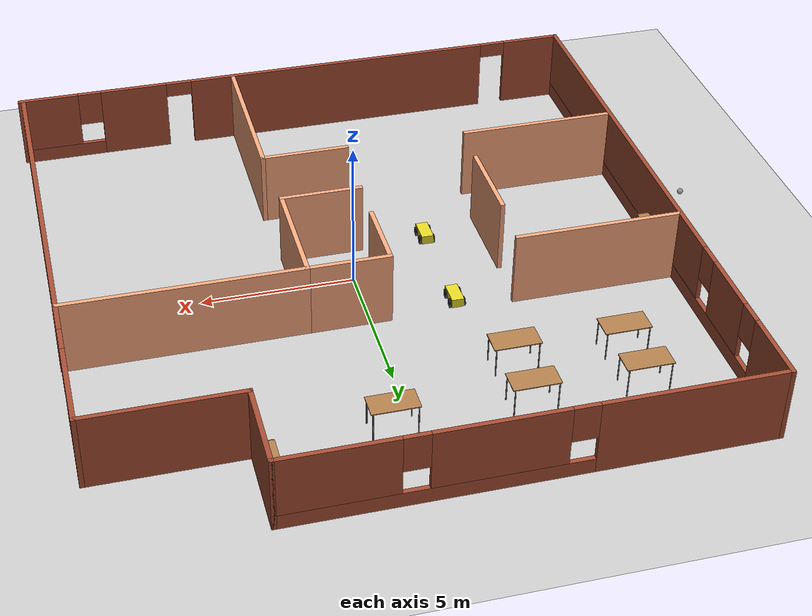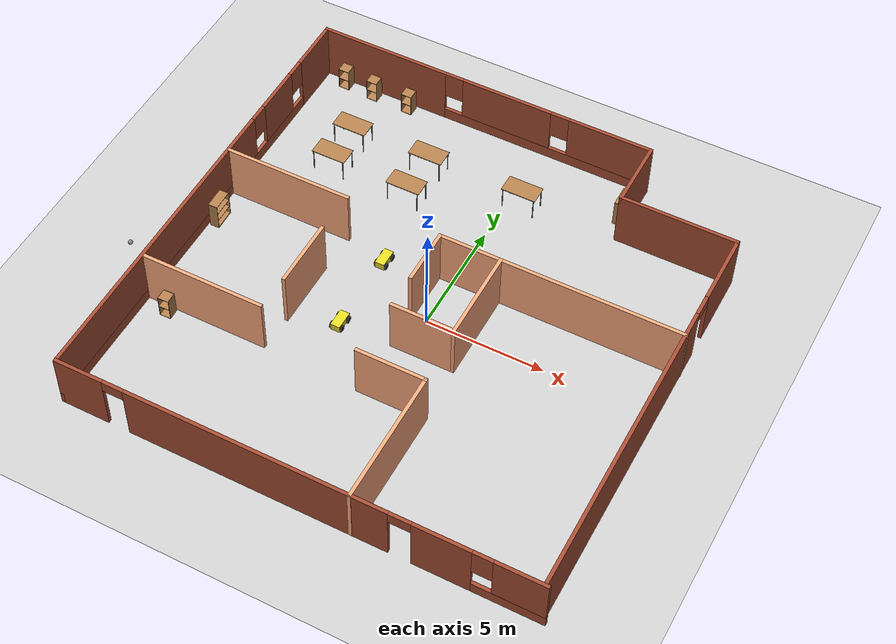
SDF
<sdf version="1.6">
 <world name="default">
  <plugin name="welcome" filename="libwelcome.so"/>
  <light name="sun" type="directional">
   <pose>0 0 10 0 -0 0</pose>
   <diffuse>0.8 0.8 0.8 1</diffuse>
   <specular>0.2 0.2 0.2 1</specular>
   <attenuation>
    <range>1000</range>
    <constant>0.9</constant>
    <linear>0.01</linear>
    <quadratic>0.001</quadratic>
   </attenuation>
   <direction>-0.5 0.1 -0.9</direction>
  </light>
  <model name="ground_plane">
   <static>1</static>
   <link name="link">
    <collision name="collision">
     <geometry><plane><normal>0 0 1</normal><size>100 100</size></plane></geometry>
     <surface><friction><ode><mu>100</mu><mu2>50</mu2></ode></friction></surface>
    </collision>
    <visual name="visual">
     <cast_shadows>0</cast_shadows>
     <geometry><plane><normal>0 0 1</normal><size>100 100</size></plane></geometry>
     <material>
      <script><uri>file://media/materials/scripts/gazebo.material</uri><name>Gazebo/Grey</name></script>
     </material>
    </visual>
   </link>
  </model>
  <gravity>0 0 -9.8</gravity>
  <magnetic_field>6e-06 2.3e-05 -4.2e-05</magnetic_field>
  <atmosphere type="adiabatic"/>
  <physics name="default_physics" default="0" type="ode">
   <max_step_size>0.001</max_step_size>
   <real_time_factor>1</real_time_factor>
   <real_time_update_rate>1000</real_time_update_rate>
  </physics>
  <scene><ambient>0.4 0.4 0.4 1</ambient><background>0.7 0.7 0.7 1</background><shadows>1</shadows></scene>
  <spherical_coordinates>
   <surface_model>EARTH_WGS84</surface_model>
   <latitude_deg>0</latitude_deg>
   <longitude_deg>0</longitude_deg>
   <elevation>0</elevation>
   <heading_deg>0</heading_deg>
  </spherical_coordinates>
  <model name="Workshop_Office">
   <pose>-0.23673 0.237179 0 0 -0 0</pose>
   <link name="Wall_2">
    <pose>-9.90477 0.002703 0 0 0 -1.5708</pose>
    <visual name="Wall_2_Visual_0">
     <pose>-8.81158 0 1.25 0 -0 0</pose>
     <geometry><box><size>2.37684 0.15 2.5</size></box></geometry>
     <material>
      <script><uri>file://media/materials/scripts/gazebo.material</uri><name>Gazebo/Bricks</name></script>
      <ambient>1 1 1 1</ambient>
     </material>
     <meta><layer>0</layer></meta>
    </visual>
    <collision name="Wall_2_Collision_0">
     <geometry><box><size>2.37684 0.15 2.5</size></box></geometry>
     <pose>-8.81158 0 1.25 0 -0 0</pose>
    </collision>
    <visual name="Wall_2_Visual_1">
     <pose>1.18842 0 0.25 0 -0 0</pose>
     <geometry><box><size>17.6232 0.15 0.5</size></box></geometry>
     <material>
      <script><uri>file://media/materials/scripts/gazebo.material</uri><name>Gazebo/Bricks</name></script>
      <ambient>1 1 1 1</ambient>
     </material>
     <meta><layer>0</layer></meta>
    </visual>
    <collision name="Wall_2_Collision_1">
     <geometry><box><size>17.6232 0.15 0.5</size></box></geometry>
     <pose>1.18842 0 0.25 0 -0 0</pose>
    </collision>
    <visual name="Wall_2_Visual_2">
     <pose>-5.76229 0 1.5 0 -0 0</pose>
     <geometry><box><size>2.12174 0.15 2</size></box></geometry>
     <material>
      <script><uri>file://media/materials/scripts/gazebo.material</uri><name>Gazebo/Bricks</name></script>
      <ambient>1 1 1 1</ambient>
     </material>
     <meta><layer>0</layer></meta>
    </visual>
    <collision name="Wall_2_Collision_2">
     <geometry><box><size>2.12174 0.15 2</size></box></geometry>
     <pose>-5.76229 0 1.5 0 -0 0</pose>
    </collision>
    <visual name="Wall_2_Visual_3">
     <pose>3.04929 0 1.5 0 -0 0</pose>
     <geometry><box><size>13.9014 0.15 2</size></box></geometry>
     <material>
      <script><uri>file://media/materials/scripts/gazebo.material</uri><name>Gazebo/Bricks</name></script>
      <ambient>1 1 1 1</ambient>
     </material>
     <meta><layer>0</layer></meta>
    </visual>
    <collision name="Wall_2_Collision_3">
     <geometry><box><size>13.9014 0.15 2</size></box></geometry>
     <pose>3.04929 0 1.5 0 -0 0</pose>
    </collision>
    <visual name="Wall_2_Visual_4">
     <pose>-7.22316 0 1.9 0 -0 0</pose>
     <geometry><box><size>0.8 0.15 1.2</size></box></geometry>
     <material>
      <script><uri>file://media/materials/scripts/gazebo.material</uri><name>Gazebo/Bricks</name></script>
      <ambient>1 1 1 1</ambient>
     </material>
     <meta><layer>0</layer></meta>
    </visual>
    <collision name="Wall_2_Collision_4">
     <geometry><box><size>0.8 0.15 1.2</size></box></geometry>
     <pose>-7.22316 0 1.9 0 -0 0</pose>
    </collision>
    <visual name="Wall_2_Visual_5">
     <pose>-4.30143 0 1.9 0 -0 0</pose>
     <geometry><box><size>0.8 0.15 1.2</size></box></geometry>
     <material>
      <script><uri>file://media/materials/scripts/gazebo.material</uri><name>Gazebo/Bricks</name></script>
      <ambient>1 1 1 1</ambient>
     </material>
     <meta><layer>0</layer></meta>
    </visual>
    <collision name="Wall_2_Collision_5">
     <geometry><box><size>0.8 0.15 1.2</size></box></geometry>
     <pose>-4.30143 0 1.9 0 -0 0</pose>
    </collision>
   </link>
   <link name="Wall_3">
    <pose>0 -9.9223 0 0 -0 0</pose>
    <visual name="Wall_3_Visual_0">
     <pose>-8.93023 0 1.25 0 -0 0</pose>
     <geometry><box><size>2.09908 0.15 2.5</size></box></geometry>
     <material>
      <script><uri>file://media/materials/scripts/gazebo.material</uri><name>Gazebo/Bricks</name></script>
      <ambient>1 1 1 1</ambient>
     </material>
     <meta><layer>0</layer></meta>
    </visual>
    <collision name="Wall_3_Collision_0">
     <geometry><box><size>2.09908 0.15 2.5</size></box></geometry>
     <pose>-8.93023 0 1.25 0 -0 0</pose>
    </collision>
    <visual name="Wall_3_Visual_1">
     <pose>-1.56113 0 1.25 0 -0 0</pose>
     <geometry><box><size>10.8391 0.15 2.5</size></box></geometry>
     <material>
      <script><uri>file://media/materials/scripts/gazebo.material</uri><name>Gazebo/Bricks</name></script>
      <ambient>1 1 1 1</ambient>
     </material>
     <meta><layer>0</layer></meta>
    </visual>
    <collision name="Wall_3_Collision_1">
     <geometry><box><size>10.8391 0.15 2.5</size></box></geometry>
     <pose>-1.56113 0 1.25 0 -0 0</pose>
    </collision>
    <visual name="Wall_3_Visual_2">
     <pose>5.92474 0 1.25 0 -0 0</pose>
     <geometry><box><size>2.33261 0.15 2.5</size></box></geometry>
     <material>
      <script><uri>file://media/materials/scripts/gazebo.material</uri><name>Gazebo/Bricks</name></script>
      <ambient>1 1 1 1</ambient>
     </material>
     <meta><layer>0</layer></meta>
    </visual>
    <collision name="Wall_3_Collision_2">
     <geometry><box><size>2.33261 0.15 2.5</size></box></geometry>
     <pose>5.92474 0 1.25 0 -0 0</pose>
    </collision>
    <visual name="Wall_3_Visual_3">
     <pose>8.53541 0 0.25 0 -0 0</pose>
     <geometry><box><size>2.88873 0.15 0.5</size></box></geometry>
     <material>
      <script><uri>file://media/materials/scripts/gazebo.material</uri><name>Gazebo/Bricks</name></script>
      <ambient>1 1 1 1</ambient>
     </material>
     <meta><layer>0</layer></meta>
    </visual>
    <collision name="Wall_3_Collision_3">
     <geometry><box><size>2.88873 0.15 0.5</size></box></geometry>
     <pose>8.53541 0 0.25 0 -0 0</pose>
    </collision>
    <visual name="Wall_3_Visual_4">
     <pose>8.93541 0 1.5 0 -0 0</pose>
     <geometry><box><size>2.08873 0.15 2</size></box></geometry>
     <material>
      <script><uri>file://media/materials/scripts/gazebo.material</uri><name>Gazebo/Bricks</name></script>
      <ambient>1 1 1 1</ambient>
     </material>
     <meta><layer>0</layer></meta>
    </visual>
    <collision name="Wall_3_Collision_4">
     <geometry><box><size>2.08873 0.15 2</size></box></geometry>
     <pose>8.93541 0 1.5 0 -0 0</pose>
    </collision>
    <visual name="Wall_3_Visual_5">
     <pose>7.49104 0 1.9 0 -0 0</pose>
     <geometry><box><size>0.8 0.15 1.2</size></box></geometry>
     <material>
      <script><uri>file://media/materials/scripts/gazebo.material</uri><name>Gazebo/Bricks</name></script>
      <ambient>1 1 1 1</ambient>
     </material>
     <meta><layer>0</layer></meta>
    </visual>
    <collision name="Wall_3_Collision_5">
     <geometry><box><size>0.8 0.15 1.2</size></box></geometry>
     <pose>7.49104 0 1.9 0 -0 0</pose>
    </collision>
    <visual name="Wall_3_Visual_6">
     <pose>-7.4307 0 2.25 0 -0 0</pose>
     <geometry><box><size>0.9 0.15 0.5</size></box></geometry>
     <material>
      <script><uri>file://media/materials/scripts/gazebo.material</uri><name>Gazebo/Bricks</name></script>
      <ambient>1 1 1 1</ambient>
     </material>
     <meta><layer>0</layer></meta>
    </visual>
    <collision name="Wall_3_Collision_6">
     <geometry><box><size>0.9 0.15 0.5</size></box></geometry>
     <pose>-7.4307 0 2.25 0 -0 0</pose>
    </collision>
    <visual name="Wall_3_Visual_7">
     <pose>4.30844 0 2.25 0 -0 0</pose>
     <geometry><box><size>0.9 0.15 0.5</size></box></geometry>
     <material>
      <script><uri>file://media/materials/scripts/gazebo.material</uri><name>Gazebo/Bricks</name></script>
      <ambient>1 1 1 1</ambient>
     </material>
     <meta><layer>0</layer></meta>
    </visual>
    <collision name="Wall_3_Collision_7">
     <geometry><box><size>0.9 0.15 0.5</size></box></geometry>
     <pose>4.30844 0 2.25 0 -0 0</pose>
    </collision>
   </link>
   <link name="Wall_35">
    <collision name="Wall_35_Collision">
     <geometry><box><size>5.25 0.15 2.5</size></box></geometry>
     <pose>0 0 1.25 0 -0 0</pose>
    </collision>
    <visual name="Wall_35_Visual">
     <pose>0 0 1.25 0 -0 0</pose>
     <geometry><box><size>5.25 0.15 2.5</size></box></geometry>
     <material>
      <script><uri>file://media/materials/scripts/gazebo.material</uri><name>Gazebo/Grey</name></script>
      <ambient>1 0.666667 0.498039 1</ambient>
     </material>
     <meta><layer>0</layer></meta>
    </visual>
    <pose>-7.22637 -4.21655 0 0 -0 0</pose>
   </link>
   <link name="Wall_38">
    <collision name="Wall_38_Collision">
     <geometry><box><size>5.75 0.15 2.5</size></box></geometry>
     <pose>0 0 1.25 0 -0 0</pose>
    </collision>
    <visual name="Wall_38_Visual">
     <pose>0 0 1.25 0 -0 0</pose>
     <geometry><box><size>5.75 0.15 2.5</size></box></geometry>
     <material>
      <script><uri>file://media/materials/scripts/gazebo.material</uri><name>Gazebo/Grey</name></script>
      <ambient>1 0.666667 0.498039 1</ambient>
     </material>
     <meta><layer>0</layer></meta>
    </visual>
    <pose>2.34244 -7.1277 0 0 0 -1.5708</pose>
   </link>
   <link name="Wall_40">
    <collision name="Wall_40_Collision">
     <geometry><box><size>2.75 0.15 2.5</size></box></geometry>
     <pose>0 0 1.25 0 -0 0</pose>
    </collision>
    <visual name="Wall_40_Visual">
     <pose>0 0 1.25 0 -0 0</pose>
     <geometry><box><size>2.75 0.15 2.5</size></box></geometry>
     <material>
      <script><uri>file://media/materials/scripts/gazebo.material</uri><name>Gazebo/Grey</name></script>
      <ambient>1 0.666667 0.498039 1</ambient>
     </material>
     <meta><layer>0</layer></meta>
    </visual>
    <pose>0.914936 -1.85738 0 0 -0 0</pose>
   </link>
   <link name="Wall_41">
    <collision name="Wall_41_Collision">
     <geometry><box><size>4 0.15 2.5</size></box></geometry>
     <pose>0 0 1.25 0 -0 0</pose>
    </collision>
    <visual name="Wall_41_Visual">
     <pose>0 0 1.25 0 -0 0</pose>
     <geometry><box><size>4 0.15 2.5</size></box></geometry>
     <material>
      <script><uri>file://media/materials/scripts/gazebo.material</uri><name>Gazebo/Grey</name></script>
      <ambient>1 0.666667 0.498039 1</ambient>
     </material>
     <meta><layer>0</layer></meta>
    </visual>
    <pose>2.21494 0.067617 0 0 -0 1.5708</pose>
   </link>
   <link name="Wall_48">
    <collision name="Wall_48_Collision">
     <geometry><box><size>7.75 0.15 2.5</size></box></geometry>
     <pose>0 0 1.25 0 -0 0</pose>
    </collision>
    <visual name="Wall_48_Visual">
     <pose>0 0 1.25 0 -0 0</pose>
     <geometry><box><size>7.75 0.15 2.5</size></box></geometry>
     <material>
      <script><uri>file://media/materials/scripts/gazebo.material</uri><name>Gazebo/Grey</name></script>
      <ambient>1 0.666667 0.498039 1</ambient>
     </material>
     <meta><layer>0</layer></meta>
    </visual>
    <pose>6.01494 1.99262 0 0 -0 0</pose>
   </link>
   <link name="Wall_5">
    <pose>-2.47977 9.9277 0 0 -0 0</pose>
    <visual name="Wall_5_Visual_0">
     <pose>-4.62546 0 1.25 0 -0 0</pose>
     <geometry><box><size>5.74908 0.15 2.5</size></box></geometry>
     <material>
      <script><uri>file://media/materials/scripts/gazebo.material</uri><name>Gazebo/Bricks</name></script>
      <ambient>1 1 1 1</ambient>
     </material>
     <meta><layer>0</layer></meta>
    </visual>
    <collision name="Wall_5_Collision_0">
     <geometry><box><size>5.74908 0.15 2.5</size></box></geometry>
     <pose>-4.62546 0 1.25 0 -0 0</pose>
    </collision>
    <visual name="Wall_5_Visual_1">
     <pose>2.87454 0 0.25 0 -0 0</pose>
     <geometry><box><size>9.25092 0.15 0.5</size></box></geometry>
     <material>
      <script><uri>file://media/materials/scripts/gazebo.material</uri><name>Gazebo/Bricks</name></script>
      <ambient>1 1 1 1</ambient>
     </material>
     <meta><layer>0</layer></meta>
    </visual>
    <collision name="Wall_5_Collision_1">
     <geometry><box><size>9.25092 0.15 0.5</size></box></geometry>
     <pose>2.87454 0 0.25 0 -0 0</pose>
    </collision>
    <visual name="Wall_5_Visual_2">
     <pose>1.04908 0 1.5 0 -0 0</pose>
     <geometry><box><size>4 0.15 2</size></box></geometry>
     <material>
      <script><uri>file://media/materials/scripts/gazebo.material</uri><name>Gazebo/Bricks</name></script>
      <ambient>1 1 1 1</ambient>
     </material>
     <meta><layer>0</layer></meta>
    </visual>
    <collision name="Wall_5_Collision_2">
     <geometry><box><size>4 0.15 2</size></box></geometry>
     <pose>1.04908 0 1.5 0 -0 0</pose>
    </collision>
    <visual name="Wall_5_Visual_3">
     <pose>5.67454 0 1.5 0 -0 0</pose>
     <geometry><box><size>3.65092 0.15 2</size></box></geometry>
     <material>
      <script><uri>file://media/materials/scripts/gazebo.material</uri><name>Gazebo/Bricks</name></script>
      <ambient>1 1 1 1</ambient>
     </material>
     <meta><layer>0</layer></meta>
    </visual>
    <collision name="Wall_5_Collision_3">
     <geometry><box><size>3.65092 0.15 2</size></box></geometry>
     <pose>5.67454 0 1.5 0 -0 0</pose>
    </collision>
    <visual name="Wall_5_Visual_4">
     <pose>-1.35092 0 1.9 0 -0 0</pose>
     <geometry><box><size>0.8 0.15 1.2</size></box></geometry>
     <material>
      <script><uri>file://media/materials/scripts/gazebo.material</uri><name>Gazebo/Bricks</name></script>
      <ambient>1 1 1 1</ambient>
     </material>
     <meta><layer>0</layer></meta>
    </visual>
    <collision name="Wall_5_Collision_4">
     <geometry><box><size>0.8 0.15 1.2</size></box></geometry>
     <pose>-1.35092 0 1.9 0 -0 0</pose>
    </collision>
    <visual name="Wall_5_Visual_5">
     <pose>3.44908 0 1.9 0 -0 0</pose>
     <geometry><box><size>0.8 0.15 1.2</size></box></geometry>
     <material>
      <script><uri>file://media/materials/scripts/gazebo.material</uri><name>Gazebo/Bricks</name></script>
      <ambient>1 1 1 1</ambient>
     </material>
     <meta><layer>0</layer></meta>
    </visual>
    <collision name="Wall_5_Collision_5">
     <geometry><box><size>0.8 0.15 1.2</size></box></geometry>
     <pose>3.44908 0 1.9 0 -0 0</pose>
    </collision>
   </link>
   <link name="Wall_50">
    <collision name="Wall_50_Collision">
     <geometry><box><size>5.5 0.15 2.5</size></box></geometry>
     <pose>0 0 1.25 0 -0 0</pose>
    </collision>
    <visual name="Wall_50_Visual">
     <pose>0 0 1.25 0 -0 0</pose>
     <geometry><box><size>5.5 0.15 2.5</size></box></geometry>
     <material>
      <script><uri>file://media/materials/scripts/gazebo.material</uri><name>Gazebo/Grey</name></script>
      <ambient>1 0.666667 0.498039 1</ambient>
     </material>
     <meta><layer>0</layer></meta>
    </visual>
    <pose>-7.15569 2.00847 0 0 -0 0</pose>
   </link>
   <link name="Wall_52">
    <collision name="Wall_52_Collision">
     <geometry><box><size>3 0.15 2.5</size></box></geometry>
     <pose>0 0 1.25 0 -0 0</pose>
    </collision>
    <visual name="Wall_52_Visual">
     <pose>0 0 1.25 0 -0 0</pose>
     <geometry><box><size>3 0.15 2.5</size></box></geometry>
     <material>
      <script><uri>file://media/materials/scripts/gazebo.material</uri><name>Gazebo/Grey</name></script>
      <ambient>1 0.666667 0.498039 1</ambient>
     </material>
     <meta><layer>0</layer></meta>
    </visual>
    <pose>-4.56113 -1.24261 0 0 0 -1.5708</pose>
   </link>
   <link name="Wall_54">
    <collision name="Wall_54_Collision">
     <geometry><box><size>2.75 0.15 2.5</size></box></geometry>
     <pose>0 0 1.25 0 -0 0</pose>
    </collision>
    <visual name="Wall_54_Visual">
     <pose>0 0 1.25 0 -0 0</pose>
     <geometry><box><size>2.75 0.15 2.5</size></box></geometry>
     <material>
      <script><uri>file://media/materials/scripts/gazebo.material</uri><name>Gazebo/Grey</name></script>
      <ambient>1 0.666667 0.498039 1</ambient>
     </material>
     <meta><layer>0</layer></meta>
    </visual>
    <pose>0.914936 1.99262 0 0 -0 3.14159</pose>
   </link>
   <link name="Wall_55">
    <collision name="Wall_55_Collision">
     <geometry><box><size>2.5 0.15 2.5</size></box></geometry>
     <pose>0 0 1.25 0 -0 0</pose>
    </collision>
    <visual name="Wall_55_Visual">
     <pose>0 0 1.25 0 -0 0</pose>
     <geometry><box><size>2.5 0.15 2.5</size></box></geometry>
     <material>
      <script><uri>file://media/materials/scripts/gazebo.material</uri><name>Gazebo/Grey</name></script>
      <ambient>1 0.666667 0.498039 1</ambient>
     </material>
     <meta><layer>0</layer></meta>
    </visual>
    <pose>-0.385064 0.817617 0 0 0 -1.5708</pose>
   </link>
   <link name="Wall_57">
    <collision name="Wall_57_Collision">
     <geometry><box><size>3 0.15 2.5</size></box></geometry>
     <pose>0 0 1.25 0 -0 0</pose>
    </collision>
    <visual name="Wall_57_Visual">
     <pose>0 0 1.25 0 -0 0</pose>
     <geometry><box><size>3 0.15 2.5</size></box></geometry>
     <material>
      <script><uri>file://media/materials/scripts/gazebo.material</uri><name>Gazebo/Grey</name></script>
      <ambient>1 0.666667 0.498039 1</ambient>
     </material>
     <meta><layer>0</layer></meta>
    </visual>
    <pose>0.917441 -4.3277 0 0 -0 3.14159</pose>
   </link>
   <link name="Wall_7">
    <collision name="Wall_7_Collision">
     <geometry><box><size>3 0.15 2.5</size></box></geometry>
     <pose>0 0 1.25 0 -0 0</pose>
    </collision>
    <visual name="Wall_7_Visual">
     <pose>0 0 1.25 0 -0 0</pose>
     <geometry><box><size>3 0.15 2.5</size></box></geometry>
     <material>
      <script><uri>file://media/materials/scripts/gazebo.material</uri><name>Gazebo/Bricks</name></script>
      <ambient>1 1 1 1</ambient>
     </material>
     <meta><layer>0</layer></meta>
    </visual>
    <pose>4.94523 8.5027 0 0 0 -1.5708</pose>
   </link>
   <link name="Wall_8">
    <collision name="Wall_8_Collision">
     <geometry><box><size>5 0.15 2.5</size></box></geometry>
     <pose>0 0 1.25 0 -0 0</pose>
    </collision>
    <visual name="Wall_8_Visual">
     <pose>0 0 1.25 0 -0 0</pose>
     <geometry><box><size>5 0.15 2.5</size></box></geometry>
     <material>
      <script><uri>file://media/materials/scripts/gazebo.material</uri><name>Gazebo/Bricks</name></script>
      <ambient>1 1 1 1</ambient>
     </material>
     <meta><layer>0</layer></meta>
    </visual>
    <pose>7.37023 7.0777 0 0 -0 0</pose>
   </link>
   <link name="Wall_9">
    <pose>9.79523 -1.3473 0 0 0 -1.5708</pose>
    <visual name="Wall_9_Visual_0">
     <pose>-6.9355 0 1.25 0 -0 0</pose>
     <geometry><box><size>3.12901 0.15 2.5</size></box></geometry>
     <material>
      <script><uri>file://media/materials/scripts/gazebo.material</uri><name>Gazebo/Bricks</name></script>
      <ambient>1 1 1 1</ambient>
     </material>
     <meta><layer>0</layer></meta>
    </visual>
    <collision name="Wall_9_Collision_0">
     <geometry><box><size>3.12901 0.15 2.5</size></box></geometry>
     <pose>-6.9355 0 1.25 0 -0 0</pose>
    </collision>
    <visual name="Wall_9_Visual_1">
     <pose>2.01451 0 1.25 0 -0 0</pose>
     <geometry><box><size>12.971 0.15 2.5</size></box></geometry>
     <material>
      <script><uri>file://media/materials/scripts/gazebo.material</uri><name>Gazebo/Bricks</name></script>
      <ambient>1 1 1 1</ambient>
     </material>
     <meta><layer>0</layer></meta>
    </visual>
    <collision name="Wall_9_Collision_1">
     <geometry><box><size>12.971 0.15 2.5</size></box></geometry>
     <pose>2.01451 0 1.25 0 -0 0</pose>
    </collision>
    <visual name="Wall_9_Visual_2">
     <pose>-4.92099 0 2.25 0 -0 0</pose>
     <geometry><box><size>0.9 0.15 0.5</size></box></geometry>
     <material>
      <script><uri>file://media/materials/scripts/gazebo.material</uri><name>Gazebo/Bricks</name></script>
      <ambient>1 1 1 1</ambient>
     </material>
     <meta><layer>0</layer></meta>
    </visual>
    <collision name="Wall_9_Collision_2">
     <geometry><box><size>0.9 0.15 0.5</size></box></geometry>
     <pose>-4.92099 0 2.25 0 -0 0</pose>
    </collision>
   </link>
   <static>1</static>
  </model>
  <model name="cabinet">
   <static>1</static>
   <link name="cabinet_bottom_plate">
    <inertial>
     <pose>0 0 -1 0 -0 0</pose>
     <inertia><ixx>2.05</ixx><ixy>0</ixy><ixz>0</ixz><iyy>2.05</iyy><iyz>0</iyz><izz>2.05</izz></inertia>
     <mass>25</mass>
    </inertial>
    <collision name="cabinet_bottom_plate_geom">
     <pose>0 0 0.01 0 -0 0</pose>
     <geometry><box><size>0.45 0.45 0.02</size></box></geometry>
    </collision>
    <visual name="cabinet_bottom_plate_geom_visual">
     <pose>0 0 0.01 0 -0 0</pose>
     <geometry><box><size>0.45 0.45 0.02</size></box></geometry>
     <material>
      <script><uri>file://media/materials/scripts/gazebo.material</uri><name>Gazebo/Wood</name></script>
     </material>
    </visual>
    <collision name="cabinet_bottom_plate_geom_cabinet_back_plate">
     <pose>0.235 0 0.51 0 -0 0</pose>
     <geometry><box><size>0.02 0.45 1.02</size></box></geometry>
    </collision>
    <visual name="cabinet_bottom_plate_geom_cabinet_back_plate_visual">
     <pose>0.235 0 0.51 0 -0 0</pose>
     <geometry><box><size>0.02 0.45 1.02</size></box></geometry>
     <material>
      <script><uri>file://media/materials/scripts/gazebo.material</uri><name>Gazebo/Wood</name></script>
     </material>
    </visual>
    <collision name="cabinet_bottom_plate_geom_cabinet_left_plate">
     <pose>0 0.235 0.51 0 -0 0</pose>
     <geometry><box><size>0.45 0.02 1.02</size></box></geometry>
    </collision>
    <visual name="cabinet_bottom_plate_geom_cabinet_left_plate_visual">
     <pose>0 0.235 0.51 0 -0 0</pose>
     <geometry><box><size>0.45 0.02 1.02</size></box></geometry>
     <material>
      <script><uri>file://media/materials/scripts/gazebo.material</uri><name>Gazebo/Wood</name></script>
     </material>
    </visual>
    <collision name="cabinet_bottom_plate_geom_cabinet_middle_plate">
     <pose>0 0 0.51 0 -0 0</pose>
     <geometry><box><size>0.45 0.45 0.02</size></box></geometry>
    </collision>
    <visual name="cabinet_bottom_plate_geom_cabinet_middle_plate_visual">
     <pose>0 0 0.51 0 -0 0</pose>
     <geometry><box><size>0.45 0.45 0.02</size></box></geometry>
     <material>
      <script><uri>file://media/materials/scripts/gazebo.material</uri><name>Gazebo/Wood</name></script>
     </material>
    </visual>
    <collision name="cabinet_bottom_plate_geom_cabinet_right_plate">
     <pose>0 -0.235 0.51 0 -0 0</pose>
     <geometry><box><size>0.45 0.02 1.02</size></box></geometry>
    </collision>
    <visual name="cabinet_bottom_plate_geom_cabinet_right_plate_visual">
     <pose>0 -0.235 0.51 0 -0 0</pose>
     <geometry><box><size>0.45 0.02 1.02</size></box></geometry>
     <material>
      <script><uri>file://media/materials/scripts/gazebo.material</uri><name>Gazebo/Wood</name></script>
     </material>
    </visual>
    <collision name="cabinet_bottom_plate_geom_cabinet_top_plate">
     <pose>0 0 1.01 0 -0 0</pose>
     <geometry><box><size>0.45 0.45 0.02</size></box></geometry>
    </collision>
    <visual name="cabinet_bottom_plate_geom_cabinet_top_plate_visual">
     <pose>0 0 1.01 0 -0 0</pose>
     <geometry><box><size>0.45 0.45 0.02</size></box></geometry>
     <material>
      <script><uri>file://media/materials/scripts/gazebo.material</uri><name>Gazebo/Wood</name></script>
     </material>
    </visual>
   </link>
   <pose>-9.06039 9.80342 0 0 -0 1.56104</pose>
  </model>
  <model name="cabinet_clone">
   <static>1</static>
   <link name="cabinet_bottom_plate">
    <inertial>
     <pose>0 0 -1 0 -0 0</pose>
     <inertia><ixx>2.05</ixx><ixy>0</ixy><ixz>0</ixz><iyy>2.05</iyy><iyz>0</iyz><izz>2.05</izz></inertia>
     <mass>25</mass>
    </inertial>
    <collision name="cabinet_bottom_plate_geom">
     <pose>0 0 0.01 0 -0 0</pose>
     <geometry><box><size>0.45 0.45 0.02</size></box></geometry>
    </collision>
    <visual name="cabinet_bottom_plate_geom_visual">
     <pose>0 0 0.01 0 -0 0</pose>
     <geometry><box><size>0.45 0.45 0.02</size></box></geometry>
     <material>
      <script><uri>file://media/materials/scripts/gazebo.material</uri><name>Gazebo/Wood</name></script>
     </material>
    </visual>
    <collision name="cabinet_bottom_plate_geom_cabinet_back_plate">
     <pose>0.235 0 0.51 0 -0 0</pose>
     <geometry><box><size>0.02 0.45 1.02</size></box></geometry>
    </collision>
    <visual name="cabinet_bottom_plate_geom_cabinet_back_plate_visual">
     <pose>0.235 0 0.51 0 -0 0</pose>
     <geometry><box><size>0.02 0.45 1.02</size></box></geometry>
     <material>
      <script><uri>file://media/materials/scripts/gazebo.material</uri><name>Gazebo/Wood</name></script>
     </material>
    </visual>
    <collision name="cabinet_bottom_plate_geom_cabinet_left_plate">
     <pose>0 0.235 0.51 0 -0 0</pose>
     <geometry><box><size>0.45 0.02 1.02</size></box></geometry>
    </collision>
    <visual name="cabinet_bottom_plate_geom_cabinet_left_plate_visual">
     <pose>0 0.235 0.51 0 -0 0</pose>
     <geometry><box><size>0.45 0.02 1.02</size></box></geometry>
     <material>
      <script><uri>file://media/materials/scripts/gazebo.material</uri><name>Gazebo/Wood</name></script>
     </material>
    </visual>
    <collision name="cabinet_bottom_plate_geom_cabinet_middle_plate">
     <pose>0 0 0.51 0 -0 0</pose>
     <geometry><box><size>0.45 0.45 0.02</size></box></geometry>
    </collision>
    <visual name="cabinet_bottom_plate_geom_cabinet_middle_plate_visual">
     <pose>0 0 0.51 0 -0 0</pose>
     <geometry><box><size>0.45 0.45 0.02</size></box></geometry>
     <material>
      <script><uri>file://media/materials/scripts/gazebo.material</uri><name>Gazebo/Wood</name></script>
     </material>
    </visual>
    <collision name="cabinet_bottom_plate_geom_cabinet_right_plate">
     <pose>0 -0.235 0.51 0 -0 0</pose>
     <geometry><box><size>0.45 0.02 1.02</size></box></geometry>
    </collision>
    <visual name="cabinet_bottom_plate_geom_cabinet_right_plate_visual">
     <pose>0 -0.235 0.51 0 -0 0</pose>
     <geometry><box><size>0.45 0.02 1.02</size></box></geometry>
     <material>
      <script><uri>file://media/materials/scripts/gazebo.material</uri><name>Gazebo/Wood</name></script>
     </material>
    </visual>
    <collision name="cabinet_bottom_plate_geom_cabinet_top_plate">
     <pose>0 0 1.01 0 -0 0</pose>
     <geometry><box><size>0.45 0.45 0.02</size></box></geometry>
    </collision>
    <visual name="cabinet_bottom_plate_geom_cabinet_top_plate_visual">
     <pose>0 0 1.01 0 -0 0</pose>
     <geometry><box><size>0.45 0.45 0.02</size></box></geometry>
     <material>
      <script><uri>file://media/materials/scripts/gazebo.material</uri><name>Gazebo/Wood</name></script>
     </material>
    </visual>
   </link>
   <pose>-7.68127 9.75015 0 0 -0 1.56104</pose>
  </model>
  <model name="cabinet_clone_0">
   <static>1</static>
   <link name="cabinet_bottom_plate">
    <inertial>
     <pose>0 0 -1 0 -0 0</pose>
     <inertia><ixx>2.05</ixx><ixy>0</ixy><ixz>0</ixz><iyy>2.05</iyy><iyz>0</iyz><izz>2.05</izz></inertia>
     <mass>25</mass>
    </inertial>
    <collision name="cabinet_bottom_plate_geom">
     <pose>0 0 0.01 0 -0 0</pose>
     <geometry><box><size>0.45 0.45 0.02</size></box></geometry>
    </collision>
    <visual name="cabinet_bottom_plate_geom_visual">
     <pose>0 0 0.01 0 -0 0</pose>
     <geometry><box><size>0.45 0.45 0.02</size></box></geometry>
     <material>
      <script><uri>file://media/materials/scripts/gazebo.material</uri><name>Gazebo/Wood</name></script>
     </material>
    </visual>
    <collision name="cabinet_bottom_plate_geom_cabinet_back_plate">
     <pose>0.235 0 0.51 0 -0 0</pose>
     <geometry><box><size>0.02 0.45 1.02</size></box></geometry>
    </collision>
    <visual name="cabinet_bottom_plate_geom_cabinet_back_plate_visual">
     <pose>0.235 0 0.51 0 -0 0</pose>
     <geometry><box><size>0.02 0.45 1.02</size></box></geometry>
     <material>
      <script><uri>file://media/materials/scripts/gazebo.material</uri><name>Gazebo/Wood</name></script>
     </material>
    </visual>
    <collision name="cabinet_bottom_plate_geom_cabinet_left_plate">
     <pose>0 0.235 0.51 0 -0 0</pose>
     <geometry><box><size>0.45 0.02 1.02</size></box></geometry>
    </collision>
    <visual name="cabinet_bottom_plate_geom_cabinet_left_plate_visual">
     <pose>0 0.235 0.51 0 -0 0</pose>
     <geometry><box><size>0.45 0.02 1.02</size></box></geometry>
     <material>
      <script><uri>file://media/materials/scripts/gazebo.material</uri><name>Gazebo/Wood</name></script>
     </material>
    </visual>
    <collision name="cabinet_bottom_plate_geom_cabinet_middle_plate">
     <pose>0 0 0.51 0 -0 0</pose>
     <geometry><box><size>0.45 0.45 0.02</size></box></geometry>
    </collision>
    <visual name="cabinet_bottom_plate_geom_cabinet_middle_plate_visual">
     <pose>0 0 0.51 0 -0 0</pose>
     <geometry><box><size>0.45 0.45 0.02</size></box></geometry>
     <material>
      <script><uri>file://media/materials/scripts/gazebo.material</uri><name>Gazebo/Wood</name></script>
     </material>
    </visual>
    <collision name="cabinet_bottom_plate_geom_cabinet_right_plate">
     <pose>0 -0.235 0.51 0 -0 0</pose>
     <geometry><box><size>0.45 0.02 1.02</size></box></geometry>
    </collision>
    <visual name="cabinet_bottom_plate_geom_cabinet_right_plate_visual">
     <pose>0 -0.235 0.51 0 -0 0</pose>
     <geometry><box><size>0.45 0.02 1.02</size></box></geometry>
     <material>
      <script><uri>file://media/materials/scripts/gazebo.material</uri><name>Gazebo/Wood</name></script>
     </material>
    </visual>
    <collision name="cabinet_bottom_plate_geom_cabinet_top_plate">
     <pose>0 0 1.01 0 -0 0</pose>
     <geometry><box><size>0.45 0.45 0.02</size></box></geometry>
    </collision>
    <visual name="cabinet_bottom_plate_geom_cabinet_top_plate_visual">
     <pose>0 0 1.01 0 -0 0</pose>
     <geometry><box><size>0.45 0.45 0.02</size></box></geometry>
     <material>
      <script><uri>file://media/materials/scripts/gazebo.material</uri><name>Gazebo/Wood</name></script>
     </material>
    </visual>
   </link>
   <pose>-6.01875 9.75 0 0 -0 1.56104</pose>
  </model>
  <model name="bookshelf">
   <static>1</static>
   <link name="link">
    <inertial><mass>1</mass></inertial>
    <collision name="back">
     <pose>0 0.005 0.6 0 -0 0</pose>
     <geometry><box><size>0.9 0.01 1.2</size></box></geometry>
    </collision>
    <visual name="visual1">
     <pose>0 0.005 0.6 0 -0 0</pose>
     <geometry><box><size>0.9 0.01 1.2</size></box></geometry>
     <material>
      <script><uri>file://media/materials/scripts/gazebo.material</uri><name>Gazebo/Wood</name></script>
     </material>
    </visual>
    <collision name="left_side">
     <pose>0.45 -0.195 0.6 0 -0 0</pose>
     <geometry><box><size>0.02 0.4 1.2</size></box></geometry>
    </collision>
    <visual name="visual2">
     <pose>0.45 -0.195 0.6 0 -0 0</pose>
     <geometry><box><size>0.02 0.4 1.2</size></box></geometry>
     <material>
      <script><uri>file://media/materials/scripts/gazebo.material</uri><name>Gazebo/Wood</name></script>
     </material>
    </visual>
    <collision name="right_side">
     <pose>-0.45 -0.195 0.6 0 -0 0</pose>
     <geometry><box><size>0.02 0.4 1.2</size></box></geometry>
    </collision>
    <visual name="visual3">
     <pose>-0.45 -0.195 0.6 0 -0 0</pose>
     <geometry><box><size>0.02 0.4 1.2</size></box></geometry>
     <material>
      <script><uri>file://media/materials/scripts/gazebo.material</uri><name>Gazebo/Wood</name></script>
     </material>
    </visual>
    <collision name="bottom">
     <pose>0 -0.195 0.03 0 -0 0</pose>
     <geometry><box><size>0.88 0.4 0.06</size></box></geometry>
    </collision>
    <visual name="visual4">
     <pose>0 -0.195 0.03 0 -0 0</pose>
     <geometry><box><size>0.88 0.4 0.06</size></box></geometry>
     <material>
      <script><uri>file://media/materials/scripts/gazebo.material</uri><name>Gazebo/Wood</name></script>
     </material>
    </visual>
    <collision name="top">
     <pose>0 -0.195 1.19 0 -0 0</pose>
     <geometry><box><size>0.88 0.4 0.02</size></box></geometry>
    </collision>
    <visual name="visual5">
     <pose>0 -0.195 1.19 0 -0 0</pose>
     <geometry><box><size>0.88 0.4 0.02</size></box></geometry>
     <material>
      <script><uri>file://media/materials/scripts/gazebo.material</uri><name>Gazebo/Wood</name></script>
     </material>
    </visual>
    <collision name="low_shelf">
     <pose>0 -0.195 0.43 0 -0 0</pose>
     <geometry><box><size>0.88 0.4 0.02</size></box></geometry>
    </collision>
    <visual name="visual6">
     <pose>0 -0.195 0.43 0 -0 0</pose>
     <geometry><box><size>0.88 0.4 0.02</size></box></geometry>
     <material>
      <script><uri>file://media/materials/scripts/gazebo.material</uri><name>Gazebo/Wood</name></script>
     </material>
    </visual>
    <collision name="high_shelf">
     <pose>0 -0.195 0.8 0 -0 0</pose>
     <geometry><box><size>0.88 0.4 0.02</size></box></geometry>
    </collision>
    <visual name="visual7">
     <pose>0 -0.195 0.8 0 -0 0</pose>
     <geometry><box><size>0.88 0.4 0.02</size></box></geometry>
     <material>
      <script><uri>file://media/materials/scripts/gazebo.material</uri><name>Gazebo/Wood</name></script>
     </material>
    </visual>
   </link>
   <pose>4.60553 8.4766 0 0 0 -1.56529</pose>
  </model>
  <model name="table">
   <static>1</static>
   <link name="link">
    <collision name="surface">
     <pose>0 0 1 0 -0 0</pose>
     <geometry><box><size>1.5 0.8 0.03</size></box></geometry>
     <surface><friction><ode><mu>0.6</mu><mu2>0.6</mu2></ode></friction></surface>
    </collision>
    <visual name="visual1">
     <pose>0 0 1 0 -0 0</pose>
     <geometry><box><size>1.5 0.8 0.03</size></box></geometry>
     <material>
      <script><uri>file://media/materials/scripts/gazebo.material</uri><name>Gazebo/Wood</name></script>
     </material>
    </visual>
    <collision name="front_left_leg">
     <pose>0.68 0.38 0.5 0 -0 0</pose>
     <geometry><cylinder><radius>0.02</radius><length>1</length></cylinder></geometry>
    </collision>
    <visual name="front_left_leg">
     <pose>0.68 0.38 0.5 0 -0 0</pose>
     <geometry><cylinder><radius>0.02</radius><length>1</length></cylinder></geometry>
     <material>
      <script><uri>file://media/materials/scripts/gazebo.material</uri><name>Gazebo/Grey</name></script>
     </material>
    </visual>
    <collision name="front_right_leg">
     <pose>0.68 -0.38 0.5 0 -0 0</pose>
     <geometry><cylinder><radius>0.02</radius><length>1</length></cylinder></geometry>
    </collision>
    <visual name="front_right_leg">
     <pose>0.68 -0.38 0.5 0 -0 0</pose>
     <geometry><cylinder><radius>0.02</radius><length>1</length></cylinder></geometry>
     <material>
      <script><uri>file://media/materials/scripts/gazebo.material</uri><name>Gazebo/Grey</name></script>
     </material>
    </visual>
    <collision name="back_right_leg">
     <pose>-0.68 -0.38 0.5 0 -0 0</pose>
     <geometry><cylinder><radius>0.02</radius><length>1</length></cylinder></geometry>
    </collision>
    <visual name="back_right_leg">
     <pose>-0.68 -0.38 0.5 0 -0 0</pose>
     <geometry><cylinder><radius>0.02</radius><length>1</length></cylinder></geometry>
     <material>
      <script><uri>file://media/materials/scripts/gazebo.material</uri><name>Gazebo/Grey</name></script>
     </material>
    </visual>
    <collision name="back_left_leg">
     <pose>-0.68 0.38 0.5 0 -0 0</pose>
     <geometry><cylinder><radius>0.02</radius><length>1</length></cylinder></geometry>
    </collision>
    <visual name="back_left_leg">
     <pose>-0.68 0.38 0.5 0 -0 0</pose>
     <geometry><cylinder><radius>0.02</radius><length>1</length></cylinder></geometry>
     <material>
      <script><uri>file://media/materials/scripts/gazebo.material</uri><name>Gazebo/Grey</name></script>
     </material>
    </visual>
   </link>
   <pose>-7.19369 7.0731 0 0 -0 0</pose>
  </model>
  <model name="table_0">
   <static>1</static>
   <link name="link">
    <collision name="surface">
     <pose>0 0 1 0 -0 0</pose>
     <geometry><box><size>1.5 0.8 0.03</size></box></geometry>
     <surface><friction><ode><mu>0.6</mu><mu2>0.6</mu2></ode></friction></surface>
    </collision>
    <visual name="visual1">
     <pose>0 0 1 0 -0 0</pose>
     <geometry><box><size>1.5 0.8 0.03</size></box></geometry>
     <material>
      <script><uri>file://media/materials/scripts/gazebo.material</uri><name>Gazebo/Wood</name></script>
     </material>
    </visual>
    <collision name="front_left_leg">
     <pose>0.68 0.38 0.5 0 -0 0</pose>
     <geometry><cylinder><radius>0.02</radius><length>1</length></cylinder></geometry>
    </collision>
    <visual name="front_left_leg">
     <pose>0.68 0.38 0.5 0 -0 0</pose>
     <geometry><cylinder><radius>0.02</radius><length>1</length></cylinder></geometry>
     <material>
      <script><uri>file://media/materials/scripts/gazebo.material</uri><name>Gazebo/Grey</name></script>
     </material>
    </visual>
    <collision name="front_right_leg">
     <pose>0.68 -0.38 0.5 0 -0 0</pose>
     <geometry><cylinder><radius>0.02</radius><length>1</length></cylinder></geometry>
    </collision>
    <visual name="front_right_leg">
     <pose>0.68 -0.38 0.5 0 -0 0</pose>
     <geometry><cylinder><radius>0.02</radius><length>1</length></cylinder></geometry>
     <material>
      <script><uri>file://media/materials/scripts/gazebo.material</uri><name>Gazebo/Grey</name></script>
     </material>
    </visual>
    <collision name="back_right_leg">
     <pose>-0.68 -0.38 0.5 0 -0 0</pose>
     <geometry><cylinder><radius>0.02</radius><length>1</length></cylinder></geometry>
    </collision>
    <visual name="back_right_leg">
     <pose>-0.68 -0.38 0.5 0 -0 0</pose>
     <geometry><cylinder><radius>0.02</radius><length>1</length></cylinder></geometry>
     <material>
      <script><uri>file://media/materials/scripts/gazebo.material</uri><name>Gazebo/Grey</name></script>
     </material>
    </visual>
    <collision name="back_left_leg">
     <pose>-0.68 0.38 0.5 0 -0 0</pose>
     <geometry><cylinder><radius>0.02</radius><length>1</length></cylinder></geometry>
    </collision>
    <visual name="back_left_leg">
     <pose>-0.68 0.38 0.5 0 -0 0</pose>
     <geometry><cylinder><radius>0.02</radius><length>1</length></cylinder></geometry>
     <material>
      <script><uri>file://media/materials/scripts/gazebo.material</uri><name>Gazebo/Grey</name></script>
     </material>
    </visual>
   </link>
   <pose>-7.17578 5.33913 0 0 -0 0</pose>
  </model>
  <model name="table_1">
   <static>1</static>
   <link name="link">
    <collision name="surface">
     <pose>0 0 1 0 -0 0</pose>
     <geometry><box><size>1.5 0.8 0.03</size></box></geometry>
     <surface><friction><ode><mu>0.6</mu><mu2>0.6</mu2></ode></friction></surface>
    </collision>
    <visual name="visual1">
     <pose>0 0 1 0 -0 0</pose>
     <geometry><box><size>1.5 0.8 0.03</size></box></geometry>
     <material>
      <script><uri>file://media/materials/scripts/gazebo.material</uri><name>Gazebo/Wood</name></script>
     </material>
    </visual>
    <collision name="front_left_leg">
     <pose>0.68 0.38 0.5 0 -0 0</pose>
     <geometry><cylinder><radius>0.02</radius><length>1</length></cylinder></geometry>
    </collision>
    <visual name="front_left_leg">
     <pose>0.68 0.38 0.5 0 -0 0</pose>
     <geometry><cylinder><radius>0.02</radius><length>1</length></cylinder></geometry>
     <material>
      <script><uri>file://media/materials/scripts/gazebo.material</uri><name>Gazebo/Grey</name></script>
     </material>
    </visual>
    <collision name="front_right_leg">
     <pose>0.68 -0.38 0.5 0 -0 0</pose>
     <geometry><cylinder><radius>0.02</radius><length>1</length></cylinder></geometry>
    </collision>
    <visual name="front_right_leg">
     <pose>0.68 -0.38 0.5 0 -0 0</pose>
     <geometry><cylinder><radius>0.02</radius><length>1</length></cylinder></geometry>
     <material>
      <script><uri>file://media/materials/scripts/gazebo.material</uri><name>Gazebo/Grey</name></script>
     </material>
    </visual>
    <collision name="back_right_leg">
     <pose>-0.68 -0.38 0.5 0 -0 0</pose>
     <geometry><cylinder><radius>0.02</radius><length>1</length></cylinder></geometry>
    </collision>
    <visual name="back_right_leg">
     <pose>-0.68 -0.38 0.5 0 -0 0</pose>
     <geometry><cylinder><radius>0.02</radius><length>1</length></cylinder></geometry>
     <material>
      <script><uri>file://media/materials/scripts/gazebo.material</uri><name>Gazebo/Grey</name></script>
     </material>
    </visual>
    <collision name="back_left_leg">
     <pose>-0.68 0.38 0.5 0 -0 0</pose>
     <geometry><cylinder><radius>0.02</radius><length>1</length></cylinder></geometry>
    </collision>
    <visual name="back_left_leg">
     <pose>-0.68 0.38 0.5 0 -0 0</pose>
     <geometry><cylinder><radius>0.02</radius><length>1</length></cylinder></geometry>
     <material>
      <script><uri>file://media/materials/scripts/gazebo.material</uri><name>Gazebo/Grey</name></script>
     </material>
    </visual>
   </link>
   <pose>-3.66733 7.11156 0 0 -0 0</pose>
  </model>
  <model name="table_2">
   <static>1</static>
   <link name="link">
    <collision name="surface">
     <pose>0 0 1 0 -0 0</pose>
     <geometry><box><size>1.5 0.8 0.03</size></box></geometry>
     <surface><friction><ode><mu>0.6</mu><mu2>0.6</mu2></ode></friction></surface>
    </collision>
    <visual name="visual1">
     <pose>0 0 1 0 -0 0</pose>
     <geometry><box><size>1.5 0.8 0.03</size></box></geometry>
     <material>
      <script><uri>file://media/materials/scripts/gazebo.material</uri><name>Gazebo/Wood</name></script>
     </material>
    </visual>
    <collision name="front_left_leg">
     <pose>0.68 0.38 0.5 0 -0 0</pose>
     <geometry><cylinder><radius>0.02</radius><length>1</length></cylinder></geometry>
    </collision>
    <visual name="front_left_leg">
     <pose>0.68 0.38 0.5 0 -0 0</pose>
     <geometry><cylinder><radius>0.02</radius><length>1</length></cylinder></geometry>
     <material>
      <script><uri>file://media/materials/scripts/gazebo.material</uri><name>Gazebo/Grey</name></script>
     </material>
    </visual>
    <collision name="front_right_leg">
     <pose>0.68 -0.38 0.5 0 -0 0</pose>
     <geometry><cylinder><radius>0.02</radius><length>1</length></cylinder></geometry>
    </collision>
    <visual name="front_right_leg">
     <pose>0.68 -0.38 0.5 0 -0 0</pose>
     <geometry><cylinder><radius>0.02</radius><length>1</length></cylinder></geometry>
     <material>
      <script><uri>file://media/materials/scripts/gazebo.material</uri><name>Gazebo/Grey</name></script>
     </material>
    </visual>
    <collision name="back_right_leg">
     <pose>-0.68 -0.38 0.5 0 -0 0</pose>
     <geometry><cylinder><radius>0.02</radius><length>1</length></cylinder></geometry>
    </collision>
    <visual name="back_right_leg">
     <pose>-0.68 -0.38 0.5 0 -0 0</pose>
     <geometry><cylinder><radius>0.02</radius><length>1</length></cylinder></geometry>
     <material>
      <script><uri>file://media/materials/scripts/gazebo.material</uri><name>Gazebo/Grey</name></script>
     </material>
    </visual>
    <collision name="back_left_leg">
     <pose>-0.68 0.38 0.5 0 -0 0</pose>
     <geometry><cylinder><radius>0.02</radius><length>1</length></cylinder></geometry>
    </collision>
    <visual name="back_left_leg">
     <pose>-0.68 0.38 0.5 0 -0 0</pose>
     <geometry><cylinder><radius>0.02</radius><length>1</length></cylinder></geometry>
     <material>
      <script><uri>file://media/materials/scripts/gazebo.material</uri><name>Gazebo/Grey</name></script>
     </material>
    </visual>
   </link>
   <pose>-3.69516 5.25005 0 0 -0 0</pose>
  </model>
  <model name="table_3">
   <static>1</static>
   <link name="link">
    <collision name="surface">
     <pose>0 0 1 0 -0 0</pose>
     <geometry><box><size>1.5 0.8 0.03</size></box></geometry>
     <surface><friction><ode><mu>0.6</mu><mu2>0.6</mu2></ode></friction></surface>
    </collision>
    <visual name="visual1">
     <pose>0 0 1 0 -0 0</pose>
     <geometry><box><size>1.5 0.8 0.03</size></box></geometry>
     <material>
      <script><uri>file://media/materials/scripts/gazebo.material</uri><name>Gazebo/Wood</name></script>
     </material>
    </visual>
    <collision name="front_left_leg">
     <pose>0.68 0.38 0.5 0 -0 0</pose>
     <geometry><cylinder><radius>0.02</radius><length>1</length></cylinder></geometry>
    </collision>
    <visual name="front_left_leg">
     <pose>0.68 0.38 0.5 0 -0 0</pose>
     <geometry><cylinder><radius>0.02</radius><length>1</length></cylinder></geometry>
     <material>
      <script><uri>file://media/materials/scripts/gazebo.material</uri><name>Gazebo/Grey</name></script>
     </material>
    </visual>
    <collision name="front_right_leg">
     <pose>0.68 -0.38 0.5 0 -0 0</pose>
     <geometry><cylinder><radius>0.02</radius><length>1</length></cylinder></geometry>
    </collision>
    <visual name="front_right_leg">
     <pose>0.68 -0.38 0.5 0 -0 0</pose>
     <geometry><cylinder><radius>0.02</radius><length>1</length></cylinder></geometry>
     <material>
      <script><uri>file://media/materials/scripts/gazebo.material</uri><name>Gazebo/Grey</name></script>
     </material>
    </visual>
    <collision name="back_right_leg">
     <pose>-0.68 -0.38 0.5 0 -0 0</pose>
     <geometry><cylinder><radius>0.02</radius><length>1</length></cylinder></geometry>
    </collision>
    <visual name="back_right_leg">
     <pose>-0.68 -0.38 0.5 0 -0 0</pose>
     <geometry><cylinder><radius>0.02</radius><length>1</length></cylinder></geometry>
     <material>
      <script><uri>file://media/materials/scripts/gazebo.material</uri><name>Gazebo/Grey</name></script>
     </material>
    </visual>
    <collision name="back_left_leg">
     <pose>-0.68 0.38 0.5 0 -0 0</pose>
     <geometry><cylinder><radius>0.02</radius><length>1</length></cylinder></geometry>
    </collision>
    <visual name="back_left_leg">
     <pose>-0.68 0.38 0.5 0 -0 0</pose>
     <geometry><cylinder><radius>0.02</radius><length>1</length></cylinder></geometry>
     <material>
      <script><uri>file://media/materials/scripts/gazebo.material</uri><name>Gazebo/Grey</name></script>
     </material>
    </visual>
   </link>
   <pose>0.579247 7.117 0 0 -0 0</pose>
  </model>
  <model name="bookshelf_0">
   <static>1</static>
   <link name="link">
    <inertial><mass>1</mass></inertial>
    <collision name="back">
     <pose>0 0.005 0.6 0 -0 0</pose>
     <geometry><box><size>0.9 0.01 1.2</size></box></geometry>
    </collision>
    <visual name="visual1">
     <pose>0 0.005 0.6 0 -0 0</pose>
     <geometry><box><size>0.9 0.01 1.2</size></box></geometry>
     <material>
      <script><uri>file://media/materials/scripts/gazebo.material</uri><name>Gazebo/Wood</name></script>
     </material>
    </visual>
    <collision name="left_side">
     <pose>0.45 -0.195 0.6 0 -0 0</pose>
     <geometry><box><size>0.02 0.4 1.2</size></box></geometry>
    </collision>
    <visual name="visual2">
     <pose>0.45 -0.195 0.6 0 -0 0</pose>
     <geometry><box><size>0.02 0.4 1.2</size></box></geometry>
     <material>
      <script><uri>file://media/materials/scripts/gazebo.material</uri><name>Gazebo/Wood</name></script>
     </material>
    </visual>
    <collision name="right_side">
     <pose>-0.45 -0.195 0.6 0 -0 0</pose>
     <geometry><box><size>0.02 0.4 1.2</size></box></geometry>
    </collision>
    <visual name="visual3">
     <pose>-0.45 -0.195 0.6 0 -0 0</pose>
     <geometry><box><size>0.02 0.4 1.2</size></box></geometry>
     <material>
      <script><uri>file://media/materials/scripts/gazebo.material</uri><name>Gazebo/Wood</name></script>
     </material>
    </visual>
    <collision name="bottom">
     <pose>0 -0.195 0.03 0 -0 0</pose>
     <geometry><box><size>0.88 0.4 0.06</size></box></geometry>
    </collision>
    <visual name="visual4">
     <pose>0 -0.195 0.03 0 -0 0</pose>
     <geometry><box><size>0.88 0.4 0.06</size></box></geometry>
     <material>
      <script><uri>file://media/materials/scripts/gazebo.material</uri><name>Gazebo/Wood</name></script>
     </material>
    </visual>
    <collision name="top">
     <pose>0 -0.195 1.19 0 -0 0</pose>
     <geometry><box><size>0.88 0.4 0.02</size></box></geometry>
    </collision>
    <visual name="visual5">
     <pose>0 -0.195 1.19 0 -0 0</pose>
     <geometry><box><size>0.88 0.4 0.02</size></box></geometry>
     <material>
      <script><uri>file://media/materials/scripts/gazebo.material</uri><name>Gazebo/Wood</name></script>
     </material>
    </visual>
    <collision name="low_shelf">
     <pose>0 -0.195 0.43 0 -0 0</pose>
     <geometry><box><size>0.88 0.4 0.02</size></box></geometry>
    </collision>
    <visual name="visual6">
     <pose>0 -0.195 0.43 0 -0 0</pose>
     <geometry><box><size>0.88 0.4 0.02</size></box></geometry>
     <material>
      <script><uri>file://media/materials/scripts/gazebo.material</uri><name>Gazebo/Wood</name></script>
     </material>
    </visual>
    <collision name="high_shelf">
     <pose>0 -0.195 0.8 0 -0 0</pose>
     <geometry><box><size>0.88 0.4 0.02</size></box></geometry>
    </collision>
    <visual name="visual7">
     <pose>0 -0.195 0.8 0 -0 0</pose>
     <geometry><box><size>0.88 0.4 0.02</size></box></geometry>
     <material>
      <script><uri>file://media/materials/scripts/gazebo.material</uri><name>Gazebo/Wood</name></script>
     </material>
    </visual>
   </link>
   <pose>-9.98625 0.736213 0 0 -0 1.59312</pose>
  </model>
  <model name="cabinet_0">
   <static>1</static>
   <link name="cabinet_bottom_plate">
    <inertial>
     <pose>0 0 -1 0 -0 0</pose>
     <inertia><ixx>2.05</ixx><ixy>0</ixy><ixz>0</ixz><iyy>2.05</iyy><iyz>0</iyz><izz>2.05</izz></inertia>
     <mass>25</mass>
    </inertial>
    <collision name="cabinet_bottom_plate_geom">
     <pose>0 0 0.01 0 -0 0</pose>
     <geometry><box><size>0.45 0.45 0.02</size></box></geometry>
    </collision>
    <visual name="cabinet_bottom_plate_geom_visual">
     <pose>0 0 0.01 0 -0 0</pose>
     <geometry><box><size>0.45 0.45 0.02</size></box></geometry>
     <material>
      <script><uri>file://media/materials/scripts/gazebo.material</uri><name>Gazebo/Wood</name></script>
     </material>
    </visual>
    <collision name="cabinet_bottom_plate_geom_cabinet_back_plate">
     <pose>0.235 0 0.51 0 -0 0</pose>
     <geometry><box><size>0.02 0.45 1.02</size></box></geometry>
    </collision>
    <visual name="cabinet_bottom_plate_geom_cabinet_back_plate_visual">
     <pose>0.235 0 0.51 0 -0 0</pose>
     <geometry><box><size>0.02 0.45 1.02</size></box></geometry>
     <material>
      <script><uri>file://media/materials/scripts/gazebo.material</uri><name>Gazebo/Wood</name></script>
     </material>
    </visual>
    <collision name="cabinet_bottom_plate_geom_cabinet_left_plate">
     <pose>0 0.235 0.51 0 -0 0</pose>
     <geometry><box><size>0.45 0.02 1.02</size></box></geometry>
    </collision>
    <visual name="cabinet_bottom_plate_geom_cabinet_left_plate_visual">
     <pose>0 0.235 0.51 0 -0 0</pose>
     <geometry><box><size>0.45 0.02 1.02</size></box></geometry>
     <material>
      <script><uri>file://media/materials/scripts/gazebo.material</uri><name>Gazebo/Wood</name></script>
     </material>
    </visual>
    <collision name="cabinet_bottom_plate_geom_cabinet_middle_plate">
     <pose>0 0 0.51 0 -0 0</pose>
     <geometry><box><size>0.45 0.45 0.02</size></box></geometry>
    </collision>
    <visual name="cabinet_bottom_plate_geom_cabinet_middle_plate_visual">
     <pose>0 0 0.51 0 -0 0</pose>
     <geometry><box><size>0.45 0.45 0.02</size></box></geometry>
     <material>
      <script><uri>file://media/materials/scripts/gazebo.material</uri><name>Gazebo/Wood</name></script>
     </material>
    </visual>
    <collision name="cabinet_bottom_plate_geom_cabinet_right_plate">
     <pose>0 -0.235 0.51 0 -0 0</pose>
     <geometry><box><size>0.45 0.02 1.02</size></box></geometry>
    </collision>
    <visual name="cabinet_bottom_plate_geom_cabinet_right_plate_visual">
     <pose>0 -0.235 0.51 0 -0 0</pose>
     <geometry><box><size>0.45 0.02 1.02</size></box></geometry>
     <material>
      <script><uri>file://media/materials/scripts/gazebo.material</uri><name>Gazebo/Wood</name></script>
     </material>
    </visual>
    <collision name="cabinet_bottom_plate_geom_cabinet_top_plate">
     <pose>0 0 1.01 0 -0 0</pose>
     <geometry><box><size>0.45 0.45 0.02</size></box></geometry>
    </collision>
    <visual name="cabinet_bottom_plate_geom_cabinet_top_plate_visual">
     <pose>0 0 1.01 0 -0 0</pose>
     <geometry><box><size>0.45 0.45 0.02</size></box></geometry>
     <material>
      <script><uri>file://media/materials/scripts/gazebo.material</uri><name>Gazebo/Wood</name></script>
     </material>
    </visual>
   </link>
   <pose>-9.01611 -4.34205 0 0 -0 1.59956</pose>
  </model>
  <model name="mobile_robot">
   <link name="wheel_0">
    <pose>-0.236758 -0.25 5e-06 0 1.56974 0</pose>
    <inertial>
     <mass>0.15</mass>
     <inertia><ixx>0.145833</ixx><ixy>0</ixy><ixz>0</ixz><iyy>0.145833</iyy><iyz>0</iyz><izz>0.125</izz></inertia>
    </inertial>
    <visual name="visual">
     <geometry><cylinder><radius>0.15</radius><length>0.05</length></cylinder></geometry>
     <material>
      <lighting>1</lighting>
      <script><uri>file://media/materials/scripts/gazebo.material</uri><name>Gazebo/Black</name></script>
      <shader type="pixel"><normal_map>__default__</normal_map></shader>
      <ambient>0.3 0.3 0.3 1</ambient>
      <diffuse>0.7 0.7 0.7 1</diffuse>
      <specular>0.01 0.01 0.01 1</specular>
      <emissive>0 0 0 1</emissive>
     </material>
    </visual>
    <collision name="collision">
     <geometry><cylinder><radius>0.15</radius><length>0.05</length></cylinder></geometry>
     <surface>
      <friction>
       <ode><mu>1</mu><mu2>1</mu2><fdir1>0 0 0</fdir1><slip1>0</slip1><slip2>0</slip2></ode>
       <torsional>
        <coefficient>1</coefficient>
        <patch_radius>0</patch_radius>
        <surface_radius>0</surface_radius>
        <use_patch_radius>1</use_patch_radius>
        <ode><slip>0</slip></ode>
       </torsional>
      </friction>
      <bounce><restitution_coefficient>0</restitution_coefficient><threshold>1e+06</threshold></bounce>
      <contact>
       <collide_without_contact>0</collide_without_contact>
       <collide_without_contact_bitmask>1</collide_without_contact_bitmask>
       <collide_bitmask>1</collide_bitmask>
       <ode>
        <soft_cfm>0</soft_cfm>
        <soft_erp>0.2</soft_erp>
        <kp>1e+13</kp>
        <kd>1</kd>
        <max_vel>0.01</max_vel>
        <min_depth>0</min_depth>
       </ode>
       <bullet>
        <split_impulse>1</split_impulse>
        <split_impulse_penetration_threshold>-0.01</split_impulse_penetration_threshold>
        <soft_cfm>0</soft_cfm>
        <soft_erp>0.2</soft_erp>
        <kp>1e+13</kp>
        <kd>1</kd>
       </bullet>
      </contact>
     </surface>
    </collision>
   </link>
   <link name="body">
    <pose>6e-06 0 0.064159 0 0.0001 0</pose>
    <inertial>
     <mass>1</mass>
     <inertia>
      <ixx>0.166667</ixx>
      <ixy>0</ixy>
      <ixz>0</ixz>
      <iyy>0.166667</iyy>
      <iyz>0</iyz>
      <izz>0.166667</izz>
     </inertia>
    </inertial>
    <visual name="visual">
     <geometry><box><size>0.4 0.8 0.3</size></box></geometry>
     <material>
      <lighting>1</lighting>
      <script><uri>file://media/materials/scripts/gazebo.material</uri><name>Gazebo/DarkYellow</name></script>
      <shader type="pixel"><normal_map>__default__</normal_map></shader>
      <ambient>0.3 0.3 0.3 1</ambient>
      <diffuse>0.7 0.7 0.7 1</diffuse>
      <specular>0.01 0.01 0.01 1</specular>
      <emissive>0 0 0 1</emissive>
     </material>
    </visual>
    <collision name="collision">
     <geometry><box><size>0.4 0.8 0.3</size></box></geometry>
     <surface>
      <friction>
       <ode><mu>1</mu><mu2>1</mu2><fdir1>0 0 0</fdir1><slip1>0</slip1><slip2>0</slip2></ode>
       <torsional>
        <coefficient>1</coefficient>
        <patch_radius>0</patch_radius>
        <surface_radius>0</surface_radius>
        <use_patch_radius>1</use_patch_radius>
        <ode><slip>0</slip></ode>
       </torsional>
      </friction>
      <bounce><restitution_coefficient>0</restitution_coefficient><threshold>1e+06</threshold></bounce>
      <contact>
       <collide_without_contact>0</collide_without_contact>
       <collide_without_contact_bitmask>1</collide_without_contact_bitmask>
       <collide_bitmask>1</collide_bitmask>
       <ode>
        <soft_cfm>0</soft_cfm>
        <soft_erp>0.2</soft_erp>
        <kp>1e+13</kp>
        <kd>1</kd>
        <max_vel>0.01</max_vel>
        <min_depth>0</min_depth>
       </ode>
       <bullet>
        <split_impulse>1</split_impulse>
        <split_impulse_penetration_threshold>-0.01</split_impulse_penetration_threshold>
        <soft_cfm>0</soft_cfm>
        <soft_erp>0.2</soft_erp>
        <kp>1e+13</kp>
        <kd>1</kd>
       </bullet>
      </contact>
     </surface>
    </collision>
   </link>
   <link name="wheel_1">
    <pose>0.220613 -0.25 -1e-06 0 1.56974 0</pose>
    <inertial>
     <mass>0.15</mass>
     <inertia><ixx>0.145833</ixx><ixy>0</ixy><ixz>0</ixz><iyy>0.145833</iyy><iyz>0</iyz><izz>0.125</izz></inertia>
    </inertial>
    <visual name="visual">
     <geometry><cylinder><radius>0.15</radius><length>0.05</length></cylinder></geometry>
     <material>
      <lighting>1</lighting>
      <script><uri>file://media/materials/scripts/gazebo.material</uri><name>Gazebo/Black</name></script>
      <shader type="pixel"><normal_map>__default__</normal_map></shader>
      <ambient>0.3 0.3 0.3 1</ambient>
      <diffuse>0.7 0.7 0.7 1</diffuse>
      <specular>0.01 0.01 0.01 1</specular>
      <emissive>0 0 0 1</emissive>
     </material>
    </visual>
    <collision name="collision">
     <geometry><cylinder><radius>0.15</radius><length>0.05</length></cylinder></geometry>
     <surface>
      <friction>
       <ode><mu>1</mu><mu2>1</mu2><fdir1>0 0 0</fdir1><slip1>0</slip1><slip2>0</slip2></ode>
       <torsional>
        <coefficient>1</coefficient>
        <patch_radius>0</patch_radius>
        <surface_radius>0</surface_radius>
        <use_patch_radius>1</use_patch_radius>
        <ode><slip>0</slip></ode>
       </torsional>
      </friction>
      <bounce><restitution_coefficient>0</restitution_coefficient><threshold>1e+06</threshold></bounce>
      <contact>
       <collide_without_contact>0</collide_without_contact>
       <collide_without_contact_bitmask>1</collide_without_contact_bitmask>
       <collide_bitmask>1</collide_bitmask>
       <ode>
        <soft_cfm>0</soft_cfm>
        <soft_erp>0.2</soft_erp>
        <kp>1e+13</kp>
        <kd>1</kd>
        <max_vel>0.01</max_vel>
        <min_depth>0</min_depth>
       </ode>
       <bullet>
        <split_impulse>1</split_impulse>
        <split_impulse_penetration_threshold>-0.01</split_impulse_penetration_threshold>
        <soft_cfm>0</soft_cfm>
        <soft_erp>0.2</soft_erp>
        <kp>1e+13</kp>
        <kd>1</kd>
       </bullet>
      </contact>
     </surface>
    </collision>
   </link>
   <link name="wheel_2">
    <pose>-0.232377 0.25 -1e-06 0 1.56974 0</pose>
    <inertial>
     <mass>0.15</mass>
     <inertia><ixx>0.145833</ixx><ixy>0</ixy><ixz>0</ixz><iyy>0.145833</iyy><iyz>0</iyz><izz>0.125</izz></inertia>
    </inertial>
    <visual name="visual">
     <geometry><cylinder><radius>0.15</radius><length>0.05</length></cylinder></geometry>
     <material>
      <lighting>1</lighting>
      <script><uri>file://media/materials/scripts/gazebo.material</uri><name>Gazebo/Black</name></script>
      <shader type="pixel"><normal_map>__default__</normal_map></shader>
      <ambient>0.3 0.3 0.3 1</ambient>
      <diffuse>0.7 0.7 0.7 1</diffuse>
      <specular>0.01 0.01 0.01 1</specular>
      <emissive>0 0 0 1</emissive>
     </material>
    </visual>
    <collision name="collision">
     <geometry><cylinder><radius>0.15</radius><length>0.05</length></cylinder></geometry>
     <surface>
      <friction>
       <ode><mu>1</mu><mu2>1</mu2><fdir1>0 0 0</fdir1><slip1>0</slip1><slip2>0</slip2></ode>
       <torsional>
        <coefficient>1</coefficient>
        <patch_radius>0</patch_radius>
        <surface_radius>0</surface_radius>
        <use_patch_radius>1</use_patch_radius>
        <ode><slip>0</slip></ode>
       </torsional>
      </friction>
      <bounce><restitution_coefficient>0</restitution_coefficient><threshold>1e+06</threshold></bounce>
      <contact>
       <collide_without_contact>0</collide_without_contact>
       <collide_without_contact_bitmask>1</collide_without_contact_bitmask>
       <collide_bitmask>1</collide_bitmask>
       <ode>
        <soft_cfm>0</soft_cfm>
        <soft_erp>0.2</soft_erp>
        <kp>1e+13</kp>
        <kd>1</kd>
        <max_vel>0.01</max_vel>
        <min_depth>0</min_depth>
       </ode>
       <bullet>
        <split_impulse>1</split_impulse>
        <split_impulse_penetration_threshold>-0.01</split_impulse_penetration_threshold>
        <soft_cfm>0</soft_cfm>
        <soft_erp>0.2</soft_erp>
        <kp>1e+13</kp>
        <kd>1</kd>
       </bullet>
      </contact>
     </surface>
    </collision>
   </link>
   <link name="wheel_3">
    <pose>0.22699 0.25 -1e-06 0 1.56974 0</pose>
    <inertial>
     <mass>0.15</mass>
     <inertia><ixx>0.145833</ixx><ixy>0</ixy><ixz>0</ixz><iyy>0.145833</iyy><iyz>0</iyz><izz>0.125</izz></inertia>
    </inertial>
    <visual name="visual">
     <geometry><cylinder><radius>0.15</radius><length>0.05</length></cylinder></geometry>
     <material>
      <lighting>1</lighting>
      <script><uri>file://media/materials/scripts/gazebo.material</uri><name>Gazebo/Black</name></script>
      <shader type="pixel"><normal_map>__default__</normal_map></shader>
      <ambient>0.3 0.3 0.3 1</ambient>
      <diffuse>0.7 0.7 0.7 1</diffuse>
      <specular>0.01 0.01 0.01 1</specular>
      <emissive>0 0 0 1</emissive>
     </material>
    </visual>
    <collision name="collision">
     <geometry><cylinder><radius>0.15</radius><length>0.05</length></cylinder></geometry>
     <surface>
      <friction>
       <ode><mu>1</mu><mu2>1</mu2><fdir1>0 0 0</fdir1><slip1>0</slip1><slip2>0</slip2></ode>
       <torsional>
        <coefficient>1</coefficient>
        <patch_radius>0</patch_radius>
        <surface_radius>0</surface_radius>
        <use_patch_radius>1</use_patch_radius>
        <ode><slip>0</slip></ode>
       </torsional>
      </friction>
      <bounce><restitution_coefficient>0</restitution_coefficient><threshold>1e+06</threshold></bounce>
      <contact>
       <collide_without_contact>0</collide_without_contact>
       <collide_without_contact_bitmask>1</collide_without_contact_bitmask>
       <collide_bitmask>1</collide_bitmask>
       <ode>
        <soft_cfm>0</soft_cfm>
        <soft_erp>0.2</soft_erp>
        <kp>1e+13</kp>
        <kd>1</kd>
        <max_vel>0.01</max_vel>
        <min_depth>0</min_depth>
       </ode>
       <bullet>
        <split_impulse>1</split_impulse>
        <split_impulse_penetration_threshold>-0.01</split_impulse_penetration_threshold>
        <soft_cfm>0</soft_cfm>
        <soft_erp>0.2</soft_erp>
        <kp>1e+13</kp>
        <kd>1</kd>
       </bullet>
      </contact>
     </surface>
    </collision>
   </link>
   <static>0</static>
   <pose>-2.86087 1.83302 0.149741 0 0.001075 0</pose>
  </model>
  <model name="mobile_robot_0">
   <link name="wheel_0">
    <pose>-0.236758 -0.25 5e-06 0 1.56974 0</pose>
    <inertial>
     <mass>0.15</mass>
     <inertia><ixx>0.145833</ixx><ixy>0</ixy><ixz>0</ixz><iyy>0.145833</iyy><iyz>0</iyz><izz>0.125</izz></inertia>
    </inertial>
    <visual name="visual">
     <geometry><cylinder><radius>0.15</radius><length>0.05</length></cylinder></geometry>
     <material>
      <lighting>1</lighting>
      <script><uri>file://media/materials/scripts/gazebo.material</uri><name>Gazebo/Black</name></script>
      <shader type="pixel"><normal_map>__default__</normal_map></shader>
      <ambient>0.3 0.3 0.3 1</ambient>
      <diffuse>0.7 0.7 0.7 1</diffuse>
      <specular>0.01 0.01 0.01 1</specular>
      <emissive>0 0 0 1</emissive>
     </material>
    </visual>
    <collision name="collision">
     <geometry><cylinder><radius>0.15</radius><length>0.05</length></cylinder></geometry>
     <surface>
      <friction>
       <ode><mu>1</mu><mu2>1</mu2><fdir1>0 0 0</fdir1><slip1>0</slip1><slip2>0</slip2></ode>
       <torsional>
        <coefficient>1</coefficient>
        <patch_radius>0</patch_radius>
        <surface_radius>0</surface_radius>
        <use_patch_radius>1</use_patch_radius>
        <ode><slip>0</slip></ode>
       </torsional>
      </friction>
      <bounce><restitution_coefficient>0</restitution_coefficient><threshold>1e+06</threshold></bounce>
      <contact>
       <collide_without_contact>0</collide_without_contact>
       <collide_without_contact_bitmask>1</collide_without_contact_bitmask>
       <collide_bitmask>1</collide_bitmask>
       <ode>
        <soft_cfm>0</soft_cfm>
        <soft_erp>0.2</soft_erp>
        <kp>1e+13</kp>
        <kd>1</kd>
        <max_vel>0.01</max_vel>
        <min_depth>0</min_depth>
       </ode>
       <bullet>
        <split_impulse>1</split_impulse>
        <split_impulse_penetration_threshold>-0.01</split_impulse_penetration_threshold>
        <soft_cfm>0</soft_cfm>
        <soft_erp>0.2</soft_erp>
        <kp>1e+13</kp>
        <kd>1</kd>
       </bullet>
      </contact>
     </surface>
    </collision>
   </link>
   <link name="body">
    <pose>6e-06 0 0.064159 0 0.0001 0</pose>
    <inertial>
     <mass>1</mass>
     <inertia>
      <ixx>0.166667</ixx>
      <ixy>0</ixy>
      <ixz>0</ixz>
      <iyy>0.166667</iyy>
      <iyz>0</iyz>
      <izz>0.166667</izz>
     </inertia>
    </inertial>
    <visual name="visual">
     <geometry><box><size>0.4 0.8 0.3</size></box></geometry>
     <material>
      <lighting>1</lighting>
      <script><uri>file://media/materials/scripts/gazebo.material</uri><name>Gazebo/DarkYellow</name></script>
      <shader type="pixel"><normal_map>__default__</normal_map></shader>
      <ambient>0.3 0.3 0.3 1</ambient>
      <diffuse>0.7 0.7 0.7 1</diffuse>
      <specular>0.01 0.01 0.01 1</specular>
      <emissive>0 0 0 1</emissive>
     </material>
    </visual>
    <collision name="collision">
     <geometry><box><size>0.4 0.8 0.3</size></box></geometry>
     <surface>
      <friction>
       <ode><mu>1</mu><mu2>1</mu2><fdir1>0 0 0</fdir1><slip1>0</slip1><slip2>0</slip2></ode>
       <torsional>
        <coefficient>1</coefficient>
        <patch_radius>0</patch_radius>
        <surface_radius>0</surface_radius>
        <use_patch_radius>1</use_patch_radius>
        <ode><slip>0</slip></ode>
       </torsional>
      </friction>
      <bounce><restitution_coefficient>0</restitution_coefficient><threshold>1e+06</threshold></bounce>
      <contact>
       <collide_without_contact>0</collide_without_contact>
       <collide_without_contact_bitmask>1</collide_without_contact_bitmask>
       <collide_bitmask>1</collide_bitmask>
       <ode>
        <soft_cfm>0</soft_cfm>
        <soft_erp>0.2</soft_erp>
        <kp>1e+13</kp>
        <kd>1</kd>
        <max_vel>0.01</max_vel>
        <min_depth>0</min_depth>
       </ode>
       <bullet>
        <split_impulse>1</split_impulse>
        <split_impulse_penetration_threshold>-0.01</split_impulse_penetration_threshold>
        <soft_cfm>0</soft_cfm>
        <soft_erp>0.2</soft_erp>
        <kp>1e+13</kp>
        <kd>1</kd>
       </bullet>
      </contact>
     </surface>
    </collision>
   </link>
   <link name="wheel_1">
    <pose>0.220613 -0.25 -1e-06 0 1.56974 0</pose>
    <inertial>
     <mass>0.15</mass>
     <inertia><ixx>0.145833</ixx><ixy>0</ixy><ixz>0</ixz><iyy>0.145833</iyy><iyz>0</iyz><izz>0.125</izz></inertia>
    </inertial>
    <visual name="visual">
     <geometry><cylinder><radius>0.15</radius><length>0.05</length></cylinder></geometry>
     <material>
      <lighting>1</lighting>
      <script><uri>file://media/materials/scripts/gazebo.material</uri><name>Gazebo/Black</name></script>
      <shader type="pixel"><normal_map>__default__</normal_map></shader>
      <ambient>0.3 0.3 0.3 1</ambient>
      <diffuse>0.7 0.7 0.7 1</diffuse>
      <specular>0.01 0.01 0.01 1</specular>
      <emissive>0 0 0 1</emissive>
     </material>
    </visual>
    <collision name="collision">
     <geometry><cylinder><radius>0.15</radius><length>0.05</length></cylinder></geometry>
     <surface>
      <friction>
       <ode><mu>1</mu><mu2>1</mu2><fdir1>0 0 0</fdir1><slip1>0</slip1><slip2>0</slip2></ode>
       <torsional>
        <coefficient>1</coefficient>
        <patch_radius>0</patch_radius>
        <surface_radius>0</surface_radius>
        <use_patch_radius>1</use_patch_radius>
        <ode><slip>0</slip></ode>
       </torsional>
      </friction>
      <bounce><restitution_coefficient>0</restitution_coefficient><threshold>1e+06</threshold></bounce>
      <contact>
       <collide_without_contact>0</collide_without_contact>
       <collide_without_contact_bitmask>1</collide_without_contact_bitmask>
       <collide_bitmask>1</collide_bitmask>
       <ode>
        <soft_cfm>0</soft_cfm>
        <soft_erp>0.2</soft_erp>
        <kp>1e+13</kp>
        <kd>1</kd>
        <max_vel>0.01</max_vel>
        <min_depth>0</min_depth>
       </ode>
       <bullet>
        <split_impulse>1</split_impulse>
        <split_impulse_penetration_threshold>-0.01</split_impulse_penetration_threshold>
        <soft_cfm>0</soft_cfm>
        <soft_erp>0.2</soft_erp>
        <kp>1e+13</kp>
        <kd>1</kd>
       </bullet>
      </contact>
     </surface>
    </collision>
   </link>
   <link name="wheel_2">
    <pose>-0.232377 0.25 -1e-06 0 1.56974 0</pose>
    <inertial>
     <mass>0.15</mass>
     <inertia><ixx>0.145833</ixx><ixy>0</ixy><ixz>0</ixz><iyy>0.145833</iyy><iyz>0</iyz><izz>0.125</izz></inertia>
    </inertial>
    <visual name="visual">
     <geometry><cylinder><radius>0.15</radius><length>0.05</length></cylinder></geometry>
     <material>
      <lighting>1</lighting>
      <script><uri>file://media/materials/scripts/gazebo.material</uri><name>Gazebo/Black</name></script>
      <shader type="pixel"><normal_map>__default__</normal_map></shader>
      <ambient>0.3 0.3 0.3 1</ambient>
      <diffuse>0.7 0.7 0.7 1</diffuse>
      <specular>0.01 0.01 0.01 1</specular>
      <emissive>0 0 0 1</emissive>
     </material>
    </visual>
    <collision name="collision">
     <geometry><cylinder><radius>0.15</radius><length>0.05</length></cylinder></geometry>
     <surface>
      <friction>
       <ode><mu>1</mu><mu2>1</mu2><fdir1>0 0 0</fdir1><slip1>0</slip1><slip2>0</slip2></ode>
       <torsional>
        <coefficient>1</coefficient>
        <patch_radius>0</patch_radius>
        <surface_radius>0</surface_radius>
        <use_patch_radius>1</use_patch_radius>
        <ode><slip>0</slip></ode>
       </torsional>
      </friction>
      <bounce><restitution_coefficient>0</restitution_coefficient><threshold>1e+06</threshold></bounce>
      <contact>
       <collide_without_contact>0</collide_without_contact>
       <collide_without_contact_bitmask>1</collide_without_contact_bitmask>
       <collide_bitmask>1</collide_bitmask>
       <ode>
        <soft_cfm>0</soft_cfm>
        <soft_erp>0.2</soft_erp>
        <kp>1e+13</kp>
        <kd>1</kd>
        <max_vel>0.01</max_vel>
        <min_depth>0</min_depth>
       </ode>
       <bullet>
        <split_impulse>1</split_impulse>
        <split_impulse_penetration_threshold>-0.01</split_impulse_penetration_threshold>
        <soft_cfm>0</soft_cfm>
        <soft_erp>0.2</soft_erp>
        <kp>1e+13</kp>
        <kd>1</kd>
       </bullet>
      </contact>
     </surface>
    </collision>
   </link>
   <link name="wheel_3">
    <pose>0.22699 0.25 -1e-06 0 1.56974 0</pose>
    <inertial>
     <mass>0.15</mass>
     <inertia><ixx>0.145833</ixx><ixy>0</ixy><ixz>0</ixz><iyy>0.145833</iyy><iyz>0</iyz><izz>0.125</izz></inertia>
    </inertial>
    <visual name="visual">
     <geometry><cylinder><radius>0.15</radius><length>0.05</length></cylinder></geometry>
     <material>
      <lighting>1</lighting>
      <script><uri>file://media/materials/scripts/gazebo.material</uri><name>Gazebo/Black</name></script>
      <shader type="pixel"><normal_map>__default__</normal_map></shader>
      <ambient>0.3 0.3 0.3 1</ambient>
      <diffuse>0.7 0.7 0.7 1</diffuse>
      <specular>0.01 0.01 0.01 1</specular>
      <emissive>0 0 0 1</emissive>
     </material>
    </visual>
    <collision name="collision">
     <geometry><cylinder><radius>0.15</radius><length>0.05</length></cylinder></geometry>
     <surface>
      <friction>
       <ode><mu>1</mu><mu2>1</mu2><fdir1>0 0 0</fdir1><slip1>0</slip1><slip2>0</slip2></ode>
       <torsional>
        <coefficient>1</coefficient>
        <patch_radius>0</patch_radius>
        <surface_radius>0</surface_radius>
        <use_patch_radius>1</use_patch_radius>
        <ode><slip>0</slip></ode>
       </torsional>
      </friction>
      <bounce><restitution_coefficient>0</restitution_coefficient><threshold>1e+06</threshold></bounce>
      <contact>
       <collide_without_contact>0</collide_without_contact>
       <collide_without_contact_bitmask>1</collide_without_contact_bitmask>
       <collide_bitmask>1</collide_bitmask>
       <ode>
        <soft_cfm>0</soft_cfm>
        <soft_erp>0.2</soft_erp>
        <kp>1e+13</kp>
        <kd>1</kd>
        <max_vel>0.01</max_vel>
        <min_depth>0</min_depth>
       </ode>
       <bullet>
        <split_impulse>1</split_impulse>
        <split_impulse_penetration_threshold>-0.01</split_impulse_penetration_threshold>
        <soft_cfm>0</soft_cfm>
        <soft_erp>0.2</soft_erp>
        <kp>1e+13</kp>
        <kd>1</kd>
       </bullet>
      </contact>
     </surface>
    </collision>
   </link>
   <static>0</static>
   <pose>-2.86458 -1.69552 0.149742 0 0.001069 0</pose>
  </model>
  <model name="my_ball">
   <link name="link">
    <inertial>
     <mass>1</mass>
     <inertia><ixx>0.1</ixx><ixy>0</ixy><ixz>0</ixz><iyy>0.1</iyy><iyz>0</iyz><izz>0.1</izz></inertia>
    </inertial>
    <visual name="visual">
     <geometry><sphere><radius>0.1</radius></sphere></geometry>
     <material>
      <script><name>Gazebo/Grey</name><uri>file://media/materials/scripts/gazebo.material</uri></script>
      <shader type="pixel"><normal_map>__default__</normal_map></shader>
      <ambient>1 1 1 1</ambient>
      <diffuse>1 1 1 1</diffuse>
      <specular>1 1 1 1</specular>
      <emissive>1 1 1 1</emissive>
     </material>
    </visual>
    <collision name="collision">
     <geometry><sphere><radius>0.1</radius></sphere></geometry>
     <surface>
      <friction>
       <ode><mu>1</mu><mu2>1</mu2><fdir1>0 0 0</fdir1><slip1>0</slip1><slip2>0</slip2></ode>
       <torsional>
        <coefficient>1</coefficient>
        <patch_radius>0</patch_radius>
        <surface_radius>0</surface_radius>
        <use_patch_radius>1</use_patch_radius>
        <ode><slip>0</slip></ode>
       </torsional>
      </friction>
      <bounce><restitution_coefficient>0</restitution_coefficient><threshold>1e+06</threshold></bounce>
      <contact>
       <collide_without_contact>0</collide_without_contact>
       <collide_without_contact_bitmask>1</collide_without_contact_bitmask>
       <collide_bitmask>1</collide_bitmask>
       <ode>
        <soft_cfm>0</soft_cfm>
        <soft_erp>0.2</soft_erp>
        <kp>1e+13</kp>
        <kd>1</kd>
        <max_vel>0.01</max_vel>
        <min_depth>0</min_depth>
       </ode>
       <bullet>
        <split_impulse>1</split_impulse>
        <split_impulse_penetration_threshold>-0.01</split_impulse_penetration_threshold>
        <soft_cfm>0</soft_cfm>
        <soft_erp>0.2</soft_erp>
        <kp>1e+13</kp>
        <kd>1</kd>
       </bullet>
      </contact>
     </surface>
    </collision>
   </link>
   <static>0</static>
   <pose>-12.2529 -2.09847 0.1 0 -0 0</pose>
  </model>
 </world>
</sdf>
